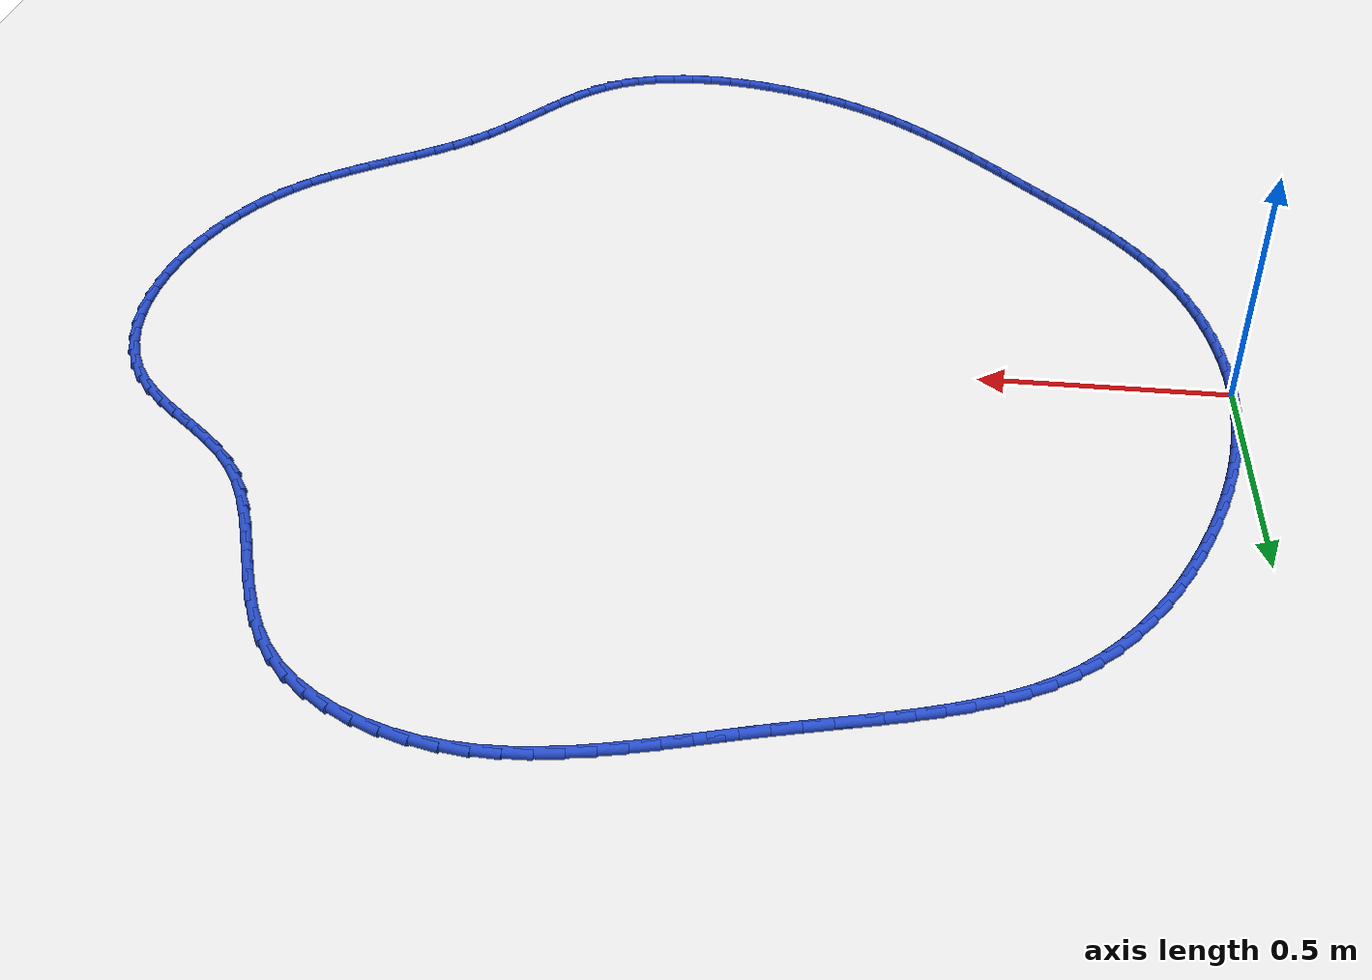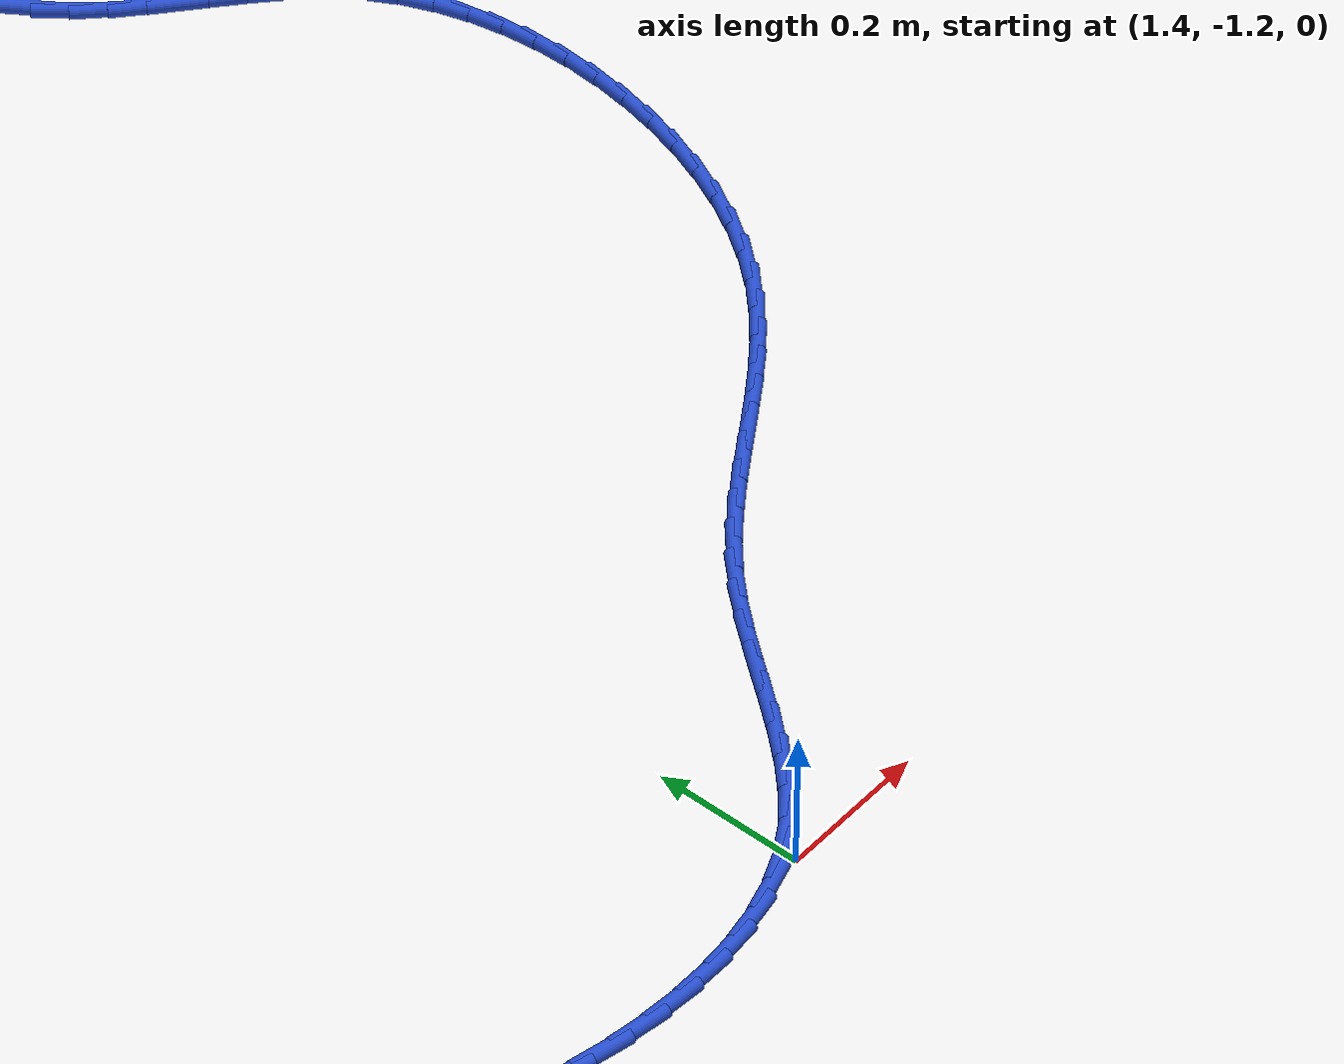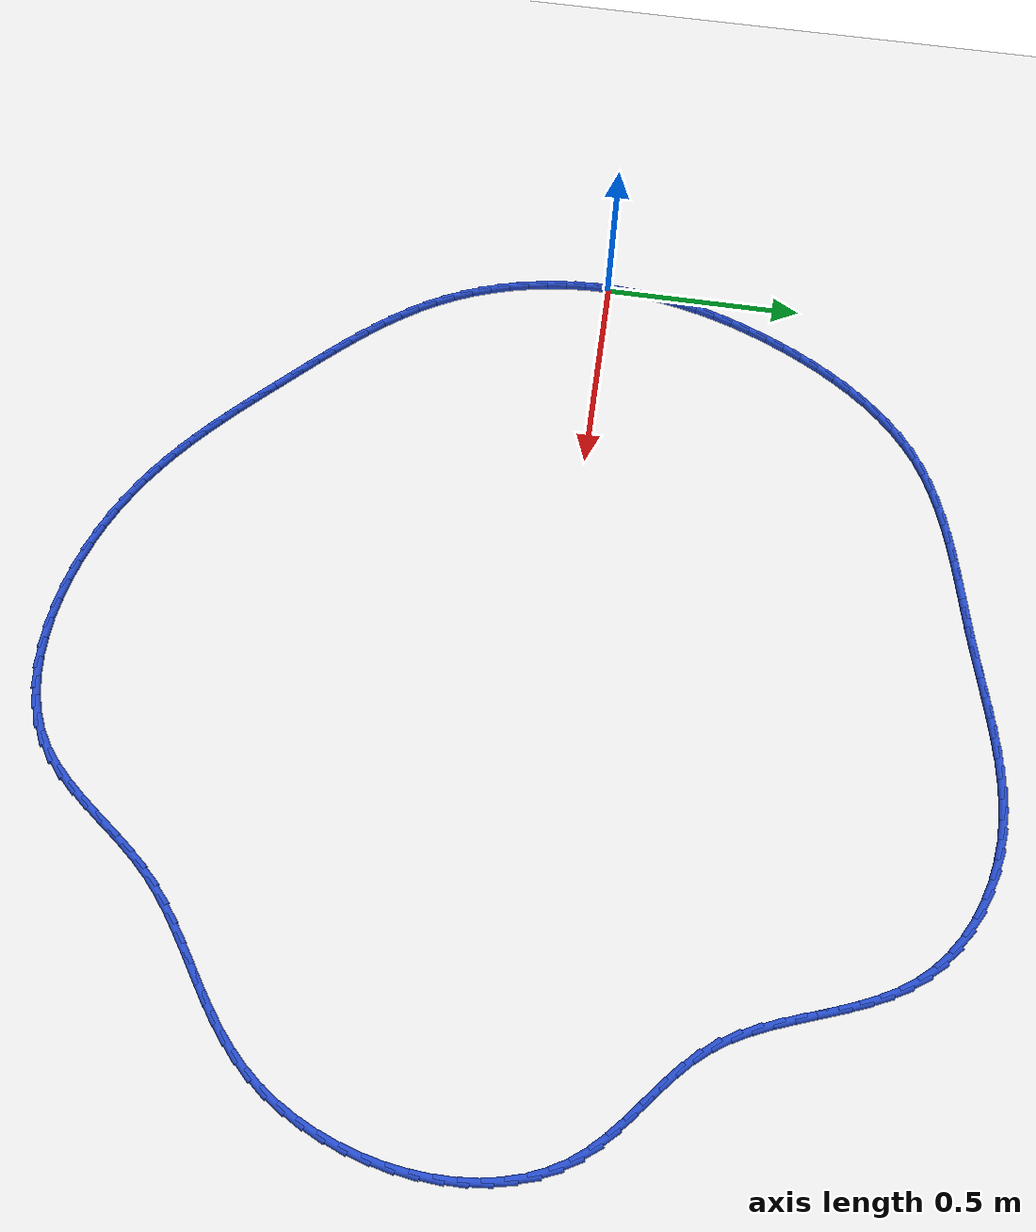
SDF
<sdf version="1.6">
 <world name="default">
  <light name="sun" type="directional">
   <pose>0 0 10 0 -0 0</pose>
   <diffuse>0.8 0.8 0.8 1</diffuse>
   <specular>0.2 0.2 0.2 1</specular>
   <attenuation>
    <range>1000</range>
    <constant>0.9</constant>
    <linear>0.01</linear>
    <quadratic>0.001</quadratic>
   </attenuation>
   <direction>-0.5 0.1 -0.9</direction>
  </light>
  <model name="ground_plane">
   <static>1</static>
   <link name="link">
    <collision name="collision">
     <geometry><plane><normal>0 0 1</normal><size>100 100</size></plane></geometry>
     <surface><friction><ode><mu>100</mu><mu2>50</mu2></ode></friction></surface>
    </collision>
    <visual name="visual">
     <cast_shadows>0</cast_shadows>
     <geometry><plane><normal>0 0 1</normal><size>100 100</size></plane></geometry>
     <material>
      <script><uri>file://media/materials/scripts/gazebo.material</uri><name>Gazebo/WhiteGlow</name></script>
     </material>
    </visual>
   </link>
  </model>
  <gravity>0 0 -9.8</gravity>
  <magnetic_field>6e-06 2.3e-05 -4.2e-05</magnetic_field>
  <atmosphere type="adiabatic"/>
  <physics name="default_physics" default="0" type="ode">
   <max_step_size>0.001</max_step_size>
   <real_time_factor>1</real_time_factor>
   <real_time_update_rate>1000</real_time_update_rate>
  </physics>
  <scene><ambient>0.4 0.4 0.4 1</ambient><background>0.7 0.7 0.7 1</background><shadows>1</shadows></scene>
  <spherical_coordinates>
   <surface_model>EARTH_WGS84</surface_model>
   <latitude_deg>0</latitude_deg>
   <longitude_deg>0</longitude_deg>
   <elevation>0</elevation>
   <heading_deg>0</heading_deg>
  </spherical_coordinates>
  <model name="line">
   <link name="link_0">
    <pose>-3.8163916471489756e-17 0.0 0.01 0 1.57 1.53081087506077</pose>
    <collision name="collision">
     <geometry><cylinder><radius>0.01</radius><length>0.08</length></cylinder></geometry>
    </collision>
    <visual name="visual">
     <material>
      <script><name>Gazebo/Blue</name><uri>file://media/materials/scripts/gazebo.material</uri></script>
     </material>
     <geometry><cylinder><radius>0.01</radius><length>0.08</length></cylinder></geometry>
    </visual>
   </link>
   <link name="link_1">
    <pose>0.001979722527505519 0.04948468118032241 0.01 0 1.57 1.4807791218871105</pose>
    <collision name="collision">
     <geometry><cylinder><radius>0.01</radius><length>0.08</length></cylinder></geometry>
    </collision>
    <visual name="visual">
     <material>
      <script><name>Gazebo/Blue</name><uri>file://media/materials/scripts/gazebo.material</uri></script>
     </material>
     <geometry><cylinder><radius>0.01</radius><length>0.08</length></cylinder></geometry>
    </visual>
   </link>
   <link name="link_2">
    <pose>0.0064161780831841105 0.09863601921336904 0.01 0 1.57 1.4322933718045248</pose>
    <collision name="collision">
     <geometry><cylinder><radius>0.01</radius><length>0.08</length></cylinder></geometry>
    </collision>
    <visual name="visual">
     <material>
      <script><name>Gazebo/Blue</name><uri>file://media/materials/scripts/gazebo.material</uri></script>
     </material>
     <geometry><cylinder><radius>0.01</radius><length>0.08</length></cylinder></geometry>
    </visual>
   </link>
   <link name="link_3">
    <pose>0.013221445217248372 0.14745588793199746 0.01 0 1.57 1.3855633104081833</pose>
    <collision name="collision">
     <geometry><cylinder><radius>0.01</radius><length>0.08</length></cylinder></geometry>
    </collision>
    <visual name="visual">
     <material>
      <script><name>Gazebo/Blue</name><uri>file://media/materials/scripts/gazebo.material</uri></script>
     </material>
     <geometry><cylinder><radius>0.01</radius><length>0.08</length></cylinder></geometry>
    </visual>
   </link>
   <link name="link_4">
    <pose>0.022307602479910926 0.1959461611690652 0.01 0 1.57 1.3407533342091134</pose>
    <collision name="collision">
     <geometry><cylinder><radius>0.01</radius><length>0.08</length></cylinder></geometry>
    </collision>
    <visual name="visual">
     <material>
      <script><name>Gazebo/Blue</name><uri>file://media/materials/scripts/gazebo.material</uri></script>
     </material>
     <geometry><cylinder><radius>0.01</radius><length>0.08</length></cylinder></geometry>
    </visual>
   </link>
   <link name="link_5">
    <pose>0.033586728421384465 0.24410871275742999 0.01 0 1.57 1.297983495147994</pose>
    <collision name="collision">
     <geometry><cylinder><radius>0.01</radius><length>0.08</length></cylinder></geometry>
    </collision>
    <visual name="visual">
     <material>
      <script><name>Gazebo/Blue</name><uri>file://media/materials/scripts/gazebo.material</uri></script>
     </material>
     <geometry><cylinder><radius>0.01</radius><length>0.08</length></cylinder></geometry>
    </visual>
   </link>
   <link name="link_6">
    <pose>0.04697090159188157 0.2919454165299492 0.01 0 1.57 1.2573325092678005</pose>
    <collision name="collision">
     <geometry><cylinder><radius>0.01</radius><length>0.08</length></cylinder></geometry>
    </collision>
    <visual name="visual">
     <material>
      <script><name>Gazebo/Blue</name><uri>file://media/materials/scripts/gazebo.material</uri></script>
     </material>
     <geometry><cylinder><radius>0.01</radius><length>0.08</length></cylinder></geometry>
    </visual>
   </link>
   <link name="link_7">
    <pose>0.06237220054161491 0.33945814631948057 0.01 0 1.57 1.2188421979531288</pose>
    <collision name="collision">
     <geometry><cylinder><radius>0.01</radius><length>0.08</length></cylinder></geometry>
    </collision>
    <visual name="visual">
     <material>
      <script><name>Gazebo/Blue</name><uri>file://media/materials/scripts/gazebo.material</uri></script>
     </material>
     <geometry><cylinder><radius>0.01</radius><length>0.08</length></cylinder></geometry>
    </visual>
   </link>
   <link name="link_8">
    <pose>0.07970270382079712 0.38664877595888164 0.01 0 1.57 1.1825227483022343</pose>
    <collision name="collision">
     <geometry><cylinder><radius>0.01</radius><length>0.08</length></cylinder></geometry>
    </collision>
    <visual name="visual">
     <material>
      <script><name>Gazebo/Blue</name><uri>file://media/materials/scripts/gazebo.material</uri></script>
     </material>
     <geometry><cylinder><radius>0.01</radius><length>0.08</length></cylinder></geometry>
    </visual>
   </link>
   <link name="link_9">
    <pose>0.09887448997964086 0.43351917928101014 0.01 0 1.57 1.147494360723241</pose>
    <collision name="collision">
     <geometry><cylinder><radius>0.01</radius><length>0.08</length></cylinder></geometry>
    </collision>
    <visual name="visual">
     <material>
      <script><name>Gazebo/Blue</name><uri>file://media/materials/scripts/gazebo.material</uri></script>
     </material>
     <geometry><cylinder><radius>0.01</radius><length>0.08</length></cylinder></geometry>
    </visual>
   </link>
   <link name="link_10">
    <pose>0.11982236632792301 0.48001433748194094 0.01 0 1.57 1.1100176047385018</pose>
    <collision name="collision">
     <geometry><cylinder><radius>0.01</radius><length>0.08</length></cylinder></geometry>
    </collision>
    <visual name="visual">
     <material>
      <script><name>Gazebo/Blue</name><uri>file://media/materials/scripts/gazebo.material</uri></script>
     </material>
     <geometry><cylinder><radius>0.01</radius><length>0.08</length></cylinder></geometry>
    </visual>
   </link>
   <link name="link_11">
    <pose>0.14257420913017707 0.525846269715818 0.01 0 1.57 1.0687088998159535</pose>
    <collision name="collision">
     <geometry><cylinder><radius>0.01</radius><length>0.08</length></cylinder></geometry>
    </collision>
    <visual name="visual">
     <material>
      <script><name>Gazebo/Blue</name><uri>file://media/materials/scripts/gazebo.material</uri></script>
     </material>
     <geometry><cylinder><radius>0.01</radius><length>0.08</length></cylinder></geometry>
    </visual>
   </link>
   <link name="link_12">
    <pose>0.16718171306497284 0.5706673749725314 0.01 0 1.57 1.0230122690982648</pose>
    <collision name="collision">
     <geometry><cylinder><radius>0.01</radius><length>0.08</length></cylinder></geometry>
    </collision>
    <visual name="visual">
     <material>
      <script><name>Gazebo/Blue</name><uri>file://media/materials/scripts/gazebo.material</uri></script>
     </material>
     <geometry><cylinder><radius>0.01</radius><length>0.08</length></cylinder></geometry>
    </visual>
   </link>
   <link name="link_13">
    <pose>0.19369657282194294 0.6141300522142797 0.01 0 1.57 0.972320734226884</pose>
    <collision name="collision">
     <geometry><cylinder><radius>0.01</radius><length>0.08</length></cylinder></geometry>
    </collision>
    <visual name="visual">
     <material>
      <script><name>Gazebo/Blue</name><uri>file://media/materials/scripts/gazebo.material</uri></script>
     </material>
     <geometry><cylinder><radius>0.01</radius><length>0.08</length></cylinder></geometry>
    </visual>
   </link>
   <link name="link_14">
    <pose>0.2221704830907201 0.6558867004032614 0.01 0 1.57 0.915989460977842</pose>
    <collision name="collision">
     <geometry><cylinder><radius>0.01</radius><length>0.08</length></cylinder></geometry>
    </collision>
    <visual name="visual">
     <material>
      <script><name>Gazebo/Blue</name><uri>file://media/materials/scripts/gazebo.material</uri></script>
     </material>
     <geometry><cylinder><radius>0.01</radius><length>0.08</length></cylinder></geometry>
    </visual>
   </link>
   <link name="link_15">
    <pose>0.25265513856093696 0.6955897185016748 0.01 0 1.57 0.8533644342717482</pose>
    <collision name="collision">
     <geometry><cylinder><radius>0.01</radius><length>0.08</length></cylinder></geometry>
    </collision>
    <visual name="visual">
     <material>
      <script><name>Gazebo/Blue</name><uri>file://media/materials/scripts/gazebo.material</uri></script>
     </material>
     <geometry><cylinder><radius>0.01</radius><length>0.08</length></cylinder></geometry>
    </visual>
   </link>
   <link name="link_16">
    <pose>0.2852022339222263 0.7328915054717189 0.01 0 1.57 0.7838338157106821</pose>
    <collision name="collision">
     <geometry><cylinder><radius>0.01</radius><length>0.08</length></cylinder></geometry>
    </collision>
    <visual name="visual">
     <material>
      <script><name>Gazebo/Blue</name><uri>file://media/materials/scripts/gazebo.material</uri></script>
     </material>
     <geometry><cylinder><radius>0.01</radius><length>0.08</length></cylinder></geometry>
    </visual>
   </link>
   <link name="link_17">
    <pose>0.31986346386422077 0.7674444602755917 0.01 0 1.57 0.7069092411978829</pose>
    <collision name="collision">
     <geometry><cylinder><radius>0.01</radius><length>0.08</length></cylinder></geometry>
    </collision>
    <visual name="visual">
     <material>
      <script><name>Gazebo/Blue</name><uri>file://media/materials/scripts/gazebo.material</uri></script>
     </material>
     <geometry><cylinder><radius>0.01</radius><length>0.08</length></cylinder></geometry>
    </visual>
   </link>
   <link name="link_18">
    <pose>0.35669052307655286 0.7989009818754916 0.01 0 1.57 0.6224150532274418</pose>
    <collision name="collision">
     <geometry><cylinder><radius>0.01</radius><length>0.08</length></cylinder></geometry>
    </collision>
    <visual name="visual">
     <material>
      <script><name>Gazebo/Blue</name><uri>file://media/materials/scripts/gazebo.material</uri></script>
     </material>
     <geometry><cylinder><radius>0.01</radius><length>0.08</length></cylinder></geometry>
    </visual>
   </link>
   <link name="link_19">
    <pose>0.39573379636541733 0.8269169212588227 0.01 0 1.57 0.5365468488485532</pose>
    <collision name="collision">
     <geometry><cylinder><radius>0.01</radius><length>0.08</length></cylinder></geometry>
    </collision>
    <visual name="visual">
     <material>
      <script><name>Gazebo/Blue</name><uri>file://media/materials/scripts/gazebo.material</uri></script>
     </material>
     <geometry><cylinder><radius>0.01</radius><length>0.08</length></cylinder></geometry>
    </visual>
   </link>
   <link name="link_20">
    <pose>0.43693913742727486 0.8514236073791587 0.01 0 1.57 0.4605530182431533</pose>
    <collision name="collision">
     <geometry><cylinder><radius>0.01</radius><length>0.08</length></cylinder></geometry>
    </collision>
    <visual name="visual">
     <material>
      <script><name>Gazebo/Blue</name><uri>file://media/materials/scripts/gazebo.material</uri></script>
     </material>
     <geometry><cylinder><radius>0.01</radius><length>0.08</length></cylinder></geometry>
    </visual>
   </link>
   <link name="link_21">
    <pose>0.4800733864922416 0.8728241355929346 0.01 0 1.57 0.39615801604458734</pose>
    <collision name="collision">
     <geometry><cylinder><radius>0.01</radius><length>0.08</length></cylinder></geometry>
    </collision>
    <visual name="visual">
     <material>
      <script><name>Gazebo/Blue</name><uri>file://media/materials/scripts/gazebo.material</uri></script>
     </material>
     <geometry><cylinder><radius>0.01</radius><length>0.08</length></cylinder></geometry>
    </visual>
   </link>
   <link name="link_22">
    <pose>0.5248858121714914 0.8915679089429837 0.01 0 1.57 0.3434493236026865</pose>
    <collision name="collision">
     <geometry><cylinder><radius>0.01</radius><length>0.08</length></cylinder></geometry>
    </collision>
    <visual name="visual">
     <material>
      <script><name>Gazebo/Blue</name><uri>file://media/materials/scripts/gazebo.material</uri></script>
     </material>
     <geometry><cylinder><radius>0.01</radius><length>0.08</length></cylinder></geometry>
    </visual>
   </link>
   <link name="link_23">
    <pose>0.5711256830761985 0.90810433047214 0.01 0 1.57 0.30213133555002225</pose>
    <collision name="collision">
     <geometry><cylinder><radius>0.01</radius><length>0.08</length></cylinder></geometry>
    </collision>
    <visual name="visual">
     <material>
      <script><name>Gazebo/Blue</name><uri>file://media/materials/scripts/gazebo.material</uri></script>
     </material>
     <geometry><cylinder><radius>0.01</radius><length>0.08</length></cylinder></geometry>
    </visual>
   </link>
   <link name="link_24">
    <pose>0.6185422678175366 0.9228828032232371 0.01 0 1.57 0.2717424104209548</pose>
    <collision name="collision">
     <geometry><cylinder><radius>0.01</radius><length>0.08</length></cylinder></geometry>
    </collision>
    <visual name="visual">
     <material>
      <script><name>Gazebo/Blue</name><uri>file://media/materials/scripts/gazebo.material</uri></script>
     </material>
     <geometry><cylinder><radius>0.01</radius><length>0.08</length></cylinder></geometry>
    </visual>
   </link>
   <link name="link_25">
    <pose>0.6668848350066798 0.9363527302391085 0.01 0 1.57 0.2518086556088177</pose>
    <collision name="collision">
     <geometry><cylinder><radius>0.01</radius><length>0.08</length></cylinder></geometry>
    </collision>
    <visual name="visual">
     <material>
      <script><name>Gazebo/Blue</name><uri>file://media/materials/scripts/gazebo.material</uri></script>
     </material>
     <geometry><cylinder><radius>0.01</radius><length>0.08</length></cylinder></geometry>
    </visual>
   </link>
   <link name="link_26">
    <pose>0.7159026532548021 0.9489635145625879 0.01 0 1.57 0.241939390597196</pose>
    <collision name="collision">
     <geometry><cylinder><radius>0.01</radius><length>0.08</length></cylinder></geometry>
    </collision>
    <visual name="visual">
     <material>
      <script><name>Gazebo/Blue</name><uri>file://media/materials/scripts/gazebo.material</uri></script>
     </material>
     <geometry><cylinder><radius>0.01</radius><length>0.08</length></cylinder></geometry>
    </visual>
   </link>
   <link name="link_27">
    <pose>0.7653449911730771 0.9611645592365086 0.01 0 1.57 0.241878161584756</pose>
    <collision name="collision">
     <geometry><cylinder><radius>0.01</radius><length>0.08</length></cylinder></geometry>
    </collision>
    <visual name="visual">
     <material>
      <script><name>Gazebo/Blue</name><uri>file://media/materials/scripts/gazebo.material</uri></script>
     </material>
     <geometry><cylinder><radius>0.01</radius><length>0.08</length></cylinder></geometry>
    </visual>
   </link>
   <link name="link_28">
    <pose>0.8149611173726793 0.9734052673037049 0.01 0 1.57 0.2515210322019817</pose>
    <collision name="collision">
     <geometry><cylinder><radius>0.01</radius><length>0.08</length></cylinder></geometry>
    </collision>
    <visual name="visual">
     <material>
      <script><name>Gazebo/Blue</name><uri>file://media/materials/scripts/gazebo.material</uri></script>
     </material>
     <geometry><cylinder><radius>0.01</radius><length>0.08</length></cylinder></geometry>
    </visual>
   </link>
   <link name="link_29">
    <pose>0.8645003147983724 0.9861349959404173 0.01 0 1.57 0.2668905871740424</pose>
    <collision name="collision">
     <geometry><cylinder><radius>0.01</radius><length>0.08</length></cylinder></geometry>
    </collision>
    <visual name="visual">
     <material>
      <script><name>Gazebo/Blue</name><uri>file://media/materials/scripts/gazebo.material</uri></script>
     </material>
     <geometry><cylinder><radius>0.01</radius><length>0.08</length></cylinder></geometry>
    </visual>
   </link>
   <link name="link_30">
    <pose>0.9137731926237459 0.9996068622212584 0.01 0 1.57 0.2748353361437529</pose>
    <collision name="collision">
     <geometry><cylinder><radius>0.01</radius><length>0.08</length></cylinder></geometry>
    </collision>
    <visual name="visual">
     <material>
      <script><name>Gazebo/Blue</name><uri>file://media/materials/scripts/gazebo.material</uri></script>
     </material>
     <geometry><cylinder><radius>0.01</radius><length>0.08</length></cylinder></geometry>
    </visual>
   </link>
   <link name="link_31">
    <pose>0.9627920031078606 1.0134287379425344 0.01 0 1.57 0.2725943795558558</pose>
    <collision name="collision">
     <geometry><cylinder><radius>0.01</radius><length>0.08</length></cylinder></geometry>
    </collision>
    <visual name="visual">
     <material>
      <script><name>Gazebo/Blue</name><uri>file://media/materials/scripts/gazebo.material</uri></script>
     </material>
     <geometry><cylinder><radius>0.01</radius><length>0.08</length></cylinder></geometry>
    </visual>
   </link>
   <link name="link_32">
    <pose>1.0116103808861336 1.0270760738810756 0.01 0 1.57 0.26001071186416236</pose>
    <collision name="collision">
     <geometry><cylinder><radius>0.01</radius><length>0.08</length></cylinder></geometry>
    </collision>
    <visual name="visual">
     <material>
      <script><name>Gazebo/Blue</name><uri>file://media/materials/scripts/gazebo.material</uri></script>
     </material>
     <geometry><cylinder><radius>0.01</radius><length>0.08</length></cylinder></geometry>
    </visual>
   </link>
   <link name="link_33">
    <pose>1.0602819605939822 1.0400243208137119 0.01 0 1.57 0.2368251089408114</pose>
    <collision name="collision">
     <geometry><cylinder><radius>0.01</radius><length>0.08</length></cylinder></geometry>
    </collision>
    <visual name="visual">
     <material>
      <script><name>Gazebo/Blue</name><uri>file://media/materials/scripts/gazebo.material</uri></script>
     </material>
     <geometry><cylinder><radius>0.01</radius><length>0.08</length></cylinder></geometry>
    </visual>
   </link>
   <link name="link_34">
    <pose>1.1088603768668228 1.0517489295172742 0.01 0 1.57 0.20271159090095395</pose>
    <collision name="collision">
     <geometry><cylinder><radius>0.01</radius><length>0.08</length></cylinder></geometry>
    </collision>
    <visual name="visual">
     <material>
      <script><name>Gazebo/Blue</name><uri>file://media/materials/scripts/gazebo.material</uri></script>
     </material>
     <geometry><cylinder><radius>0.01</radius><length>0.08</length></cylinder></geometry>
    </visual>
   </link>
   <link name="link_35">
    <pose>1.1573992643400726 1.0617253507685922 0.01 0 1.57 0.1573537947079281</pose>
    <collision name="collision">
     <geometry><cylinder><radius>0.01</radius><length>0.08</length></cylinder></geometry>
    </collision>
    <visual name="visual">
     <material>
      <script><name>Gazebo/Blue</name><uri>file://media/materials/scripts/gazebo.material</uri></script>
     </material>
     <geometry><cylinder><radius>0.01</radius><length>0.08</length></cylinder></geometry>
    </visual>
   </link>
   <link name="link_36">
    <pose>1.2059522576491486 1.0694290353444964 0.01 0 1.57 0.10057119876426046</pose>
    <collision name="collision">
     <geometry><cylinder><radius>0.01</radius><length>0.08</length></cylinder></geometry>
    </collision>
    <visual name="visual">
     <material>
      <script><name>Gazebo/Blue</name><uri>file://media/materials/scripts/gazebo.material</uri></script>
     </material>
     <geometry><cylinder><radius>0.01</radius><length>0.08</length></cylinder></geometry>
    </visual>
   </link>
   <link name="link_37">
    <pose>1.2545729914294677 1.0743354340218167 0.01 0 1.57 0.03249768492827597</pose>
    <collision name="collision">
     <geometry><cylinder><radius>0.01</radius><length>0.08</length></cylinder></geometry>
    </collision>
    <visual name="visual">
     <material>
      <script><name>Gazebo/Blue</name><uri>file://media/materials/scripts/gazebo.material</uri></script>
     </material>
     <geometry><cylinder><radius>0.01</radius><length>0.08</length></cylinder></geometry>
    </visual>
   </link>
   <link name="link_38">
    <pose>1.3033151003164465 1.0759199975773834 0.01 0 1.57 -0.04620490824820704</pose>
    <collision name="collision">
     <geometry><cylinder><radius>0.01</radius><length>0.08</length></cylinder></geometry>
    </collision>
    <visual name="visual">
     <material>
      <script><name>Gazebo/Blue</name><uri>file://media/materials/scripts/gazebo.material</uri></script>
     </material>
     <geometry><cylinder><radius>0.01</radius><length>0.08</length></cylinder></geometry>
    </visual>
   </link>
   <link name="link_39">
    <pose>1.352232218945503 1.0736581767880269 0.01 0 1.57 -0.13413293280615798</pose>
    <collision name="collision">
     <geometry><cylinder><radius>0.01</radius><length>0.08</length></cylinder></geometry>
    </collision>
    <visual name="visual">
     <material>
      <script><name>Gazebo/Blue</name><uri>file://media/materials/scripts/gazebo.material</uri></script>
     </material>
     <geometry><cylinder><radius>0.01</radius><length>0.08</length></cylinder></geometry>
    </visual>
   </link>
   <link name="link_40">
    <pose>1.401376419201328 1.0670265017133975 0.01 0 1.57 -0.22668272803391348</pose>
    <collision name="collision">
     <geometry><cylinder><radius>0.01</radius><length>0.08</length></cylinder></geometry>
    </collision>
    <visual name="visual">
     <material>
      <script><name>Gazebo/Blue</name><uri>file://media/materials/scripts/gazebo.material</uri></script>
     </material>
     <geometry><cylinder><radius>0.01</radius><length>0.08</length></cylinder></geometry>
    </visual>
   </link>
   <link name="link_41">
    <pose>1.4505266011161937 1.0556901631399138 0.01 0 1.57 -0.3190634901556683</pose>
    <collision name="collision">
     <geometry><cylinder><radius>0.01</radius><length>0.08</length></cylinder></geometry>
    </collision>
    <visual name="visual">
     <material>
      <script><name>Gazebo/Blue</name><uri>file://media/materials/scripts/gazebo.material</uri></script>
     </material>
     <geometry><cylinder><radius>0.01</radius><length>0.08</length></cylinder></geometry>
    </visual>
   </link>
   <link name="link_42">
    <pose>1.4988785211215883 1.0397170884264384 0.01 0 1.57 -0.41366919996070306</pose>
    <collision name="collision">
     <geometry><cylinder><radius>0.01</radius><length>0.08</length></cylinder></geometry>
    </collision>
    <visual name="visual">
     <material>
      <script><name>Gazebo/Blue</name><uri>file://media/materials/scripts/gazebo.material</uri></script>
     </material>
     <geometry><cylinder><radius>0.01</radius><length>0.08</length></cylinder></geometry>
    </visual>
   </link>
   <link name="link_43">
    <pose>1.5455529595109843 1.0192269857158454 0.01 0 1.57 -0.5136144983648645</pose>
    <collision name="collision">
     <geometry><cylinder><radius>0.01</radius><length>0.08</length></cylinder></geometry>
    </collision>
    <visual name="visual">
     <material>
      <script><name>Gazebo/Blue</name><uri>file://media/materials/scripts/gazebo.material</uri></script>
     </material>
     <geometry><cylinder><radius>0.01</radius><length>0.08</length></cylinder></geometry>
    </visual>
   </link>
   <link name="link_44">
    <pose>1.5896706965778555 0.9943395631510091 0.01 0 1.57 -0.6219823300720324</pose>
    <collision name="collision">
     <geometry><cylinder><radius>0.01</radius><length>0.08</length></cylinder></geometry>
    </collision>
    <visual name="visual">
     <material>
      <script><name>Gazebo/Blue</name><uri>file://media/materials/scripts/gazebo.material</uri></script>
     </material>
     <geometry><cylinder><radius>0.01</radius><length>0.08</length></cylinder></geometry>
    </visual>
   </link>
   <link name="link_45">
    <pose>1.630352512615673 0.9651745288748044 0.01 0 1.57 -0.7417502772724007</pose>
    <collision name="collision">
     <geometry><cylinder><radius>0.01</radius><length>0.08</length></cylinder></geometry>
    </collision>
    <visual name="visual">
     <material>
      <script><name>Gazebo/Blue</name><uri>file://media/materials/scripts/gazebo.material</uri></script>
     </material>
     <geometry><cylinder><radius>0.01</radius><length>0.08</length></cylinder></geometry>
    </visual>
   </link>
   <link name="link_46">
    <pose>1.6667191879179102 0.9318515910301057 0.01 0 1.57 -0.8731737706783052</pose>
    <collision name="collision">
     <geometry><cylinder><radius>0.01</radius><length>0.08</length></cylinder></geometry>
    </collision>
    <visual name="visual">
     <material>
      <script><name>Gazebo/Blue</name><uri>file://media/materials/scripts/gazebo.material</uri></script>
     </material>
     <geometry><cylinder><radius>0.01</radius><length>0.08</length></cylinder></geometry>
    </visual>
   </link>
   <link name="link_47">
    <pose>1.6980058838474383 0.8945269816575713 0.01 0 1.57 -0.994179210123533</pose>
    <collision name="collision">
     <geometry><cylinder><radius>0.01</radius><length>0.08</length></cylinder></geometry>
    </collision>
    <visual name="visual">
     <material>
      <script><name>Gazebo/Blue</name><uri>file://media/materials/scripts/gazebo.material</uri></script>
     </material>
     <geometry><cylinder><radius>0.01</radius><length>0.08</length></cylinder></geometry>
    </visual>
   </link>
   <link name="link_48">
    <pose>1.7245513964961652 0.85370934287975 0.01 0 1.57 -1.0897222913817504</pose>
    <collision name="collision">
     <geometry><cylinder><radius>0.01</radius><length>0.08</length></cylinder></geometry>
    </collision>
    <visual name="visual">
     <material>
      <script><name>Gazebo/Blue</name><uri>file://media/materials/scripts/gazebo.material</uri></script>
     </material>
     <geometry><cylinder><radius>0.01</radius><length>0.08</length></cylinder></geometry>
    </visual>
   </link>
   <link name="link_49">
    <pose>1.7473120998541447 0.8101045203612101 0.01 0 1.57 -1.1592627033562999</pose>
    <collision name="collision">
     <geometry><cylinder><radius>0.01</radius><length>0.08</length></cylinder></geometry>
    </collision>
    <visual name="visual">
     <material>
      <script><name>Gazebo/Blue</name><uri>file://media/materials/scripts/gazebo.material</uri></script>
     </material>
     <geometry><cylinder><radius>0.01</radius><length>0.08</length></cylinder></geometry>
    </visual>
   </link>
   <link name="link_50">
    <pose>1.7672511432443432 0.764420523250109 0.01 0 1.57 -1.2039484873253772</pose>
    <collision name="collision">
     <geometry><cylinder><radius>0.01</radius><length>0.08</length></cylinder></geometry>
    </collision>
    <visual name="visual">
     <material>
      <script><name>Gazebo/Blue</name><uri>file://media/materials/scripts/gazebo.material</uri></script>
     </material>
     <geometry><cylinder><radius>0.01</radius><length>0.08</length></cylinder></geometry>
    </visual>
   </link>
   <link name="link_51">
    <pose>1.7853316759897284 0.7173653606946067 0.01 0 1.57 -1.2251187419603604</pose>
    <collision name="collision">
     <geometry><cylinder><radius>0.01</radius><length>0.08</length></cylinder></geometry>
    </collision>
    <visual name="visual">
     <material>
      <script><name>Gazebo/Blue</name><uri>file://media/materials/scripts/gazebo.material</uri></script>
     </material>
     <geometry><cylinder><radius>0.01</radius><length>0.08</length></cylinder></geometry>
    </visual>
   </link>
   <link name="link_52">
    <pose>1.802516847413267 0.6696470418428605 0.01 0 1.57 -1.2235610140664208</pose>
    <collision name="collision">
     <geometry><cylinder><radius>0.01</radius><length>0.08</length></cylinder></geometry>
    </collision>
    <visual name="visual">
     <material>
      <script><name>Gazebo/Blue</name><uri>file://media/materials/scripts/gazebo.material</uri></script>
     </material>
     <geometry><cylinder><radius>0.01</radius><length>0.08</length></cylinder></geometry>
    </visual>
   </link>
   <link name="link_53">
    <pose>1.8197698068379258 0.6219735758430299 0.01 0 1.57 -1.1992203350926671</pose>
    <collision name="collision">
     <geometry><cylinder><radius>0.01</radius><length>0.08</length></cylinder></geometry>
    </collision>
    <visual name="visual">
     <material>
      <script><name>Gazebo/Blue</name><uri>file://media/materials/scripts/gazebo.material</uri></script>
     </material>
     <geometry><cylinder><radius>0.01</radius><length>0.08</length></cylinder></geometry>
    </visual>
   </link>
   <link name="link_54">
    <pose>1.8380537035866713 0.5750529718432726 0.01 0 1.57 -1.1512197904056243</pose>
    <collision name="collision">
     <geometry><cylinder><radius>0.01</radius><length>0.08</length></cylinder></geometry>
    </collision>
    <visual name="visual">
     <material>
      <script><name>Gazebo/Blue</name><uri>file://media/materials/scripts/gazebo.material</uri></script>
     </material>
     <geometry><cylinder><radius>0.01</radius><length>0.08</length></cylinder></geometry>
    </visual>
   </link>
   <link name="link_55">
    <pose>1.8583316869824724 0.5295932389917475 0.01 0 1.57 -1.0782032874842342</pose>
    <collision name="collision">
     <geometry><cylinder><radius>0.01</radius><length>0.08</length></cylinder></geometry>
    </collision>
    <visual name="visual">
     <material>
      <script><name>Gazebo/Blue</name><uri>file://media/materials/scripts/gazebo.material</uri></script>
     </material>
     <geometry><cylinder><radius>0.01</radius><length>0.08</length></cylinder></geometry>
    </visual>
   </link>
   <link name="link_56">
    <pose>1.8815669063482938 0.4863023864366133 0.01 0 1.57 -0.979154454333042</pose>
    <collision name="collision">
     <geometry><cylinder><radius>0.01</radius><length>0.08</length></cylinder></geometry>
    </collision>
    <visual name="visual">
     <material>
      <script><name>Gazebo/Blue</name><uri>file://media/materials/scripts/gazebo.material</uri></script>
     </material>
     <geometry><cylinder><radius>0.01</radius><length>0.08</length></cylinder></geometry>
    </visual>
   </link>
   <link name="link_57">
    <pose>1.908722511007104 0.44588842332602785 0.01 0 1.57 -0.8627603080321099</pose>
    <collision name="collision">
     <geometry><cylinder><radius>0.01</radius><length>0.08</length></cylinder></geometry>
    </collision>
    <visual name="visual">
     <material>
      <script><name>Gazebo/Blue</name><uri>file://media/materials/scripts/gazebo.material</uri></script>
     </material>
     <geometry><cylinder><radius>0.01</radius><length>0.08</length></cylinder></geometry>
    </visual>
   </link>
   <link name="link_58">
    <pose>1.940449605453515 0.40882923274522465 0.01 0 1.57 -0.770514575392855</pose>
    <collision name="collision">
     <geometry><cylinder><radius>0.01</radius><length>0.08</length></cylinder></geometry>
    </collision>
    <visual name="visual">
     <material>
      <script><name>Gazebo/Blue</name><uri>file://media/materials/scripts/gazebo.material</uri></script>
     </material>
     <geometry><cylinder><radius>0.01</radius><length>0.08</length></cylinder></geometry>
    </visual>
   </link>
   <link name="link_59">
    <pose>1.975854157489885 0.37446319412046747 0.01 0 1.57 -0.7141520142694131</pose>
    <collision name="collision">
     <geometry><cylinder><radius>0.01</radius><length>0.08</length></cylinder></geometry>
    </collision>
    <visual name="visual">
     <material>
      <script><name>Gazebo/Blue</name><uri>file://media/materials/scripts/gazebo.material</uri></script>
     </material>
     <geometry><cylinder><radius>0.01</radius><length>0.08</length></cylinder></geometry>
    </visual>
   </link>
   <link name="link_60">
    <pose>2.013564753231257 0.3417766285894941 0.01 0 1.57 -0.6919314941801472</pose>
    <collision name="collision">
     <geometry><cylinder><radius>0.01</radius><length>0.08</length></cylinder></geometry>
    </collision>
    <visual name="visual">
     <material>
      <script><name>Gazebo/Blue</name><uri>file://media/materials/scripts/gazebo.material</uri></script>
     </material>
     <geometry><cylinder><radius>0.01</radius><length>0.08</length></cylinder></geometry>
    </visual>
   </link>
   <link name="link_61">
    <pose>2.0522098398991466 0.3097557548591764 0.01 0 1.57 -0.7028529340440991</pose>
    <collision name="collision">
     <geometry><cylinder><radius>0.01</radius><length>0.08</length></cylinder></geometry>
    </collision>
    <visual name="visual">
     <material>
      <script><name>Gazebo/Blue</name><uri>file://media/materials/scripts/gazebo.material</uri></script>
     </material>
     <geometry><cylinder><radius>0.01</radius><length>0.08</length></cylinder></geometry>
    </visual>
   </link>
   <link name="link_62">
    <pose>2.090417864715064 0.27738679163638674 0.01 0 1.57 -0.747364796307066</pose>
    <collision name="collision">
     <geometry><cylinder><radius>0.01</radius><length>0.08</length></cylinder></geometry>
    </collision>
    <visual name="visual">
     <material>
      <script><name>Gazebo/Blue</name><uri>file://media/materials/scripts/gazebo.material</uri></script>
     </material>
     <geometry><cylinder><radius>0.01</radius><length>0.08</length></cylinder></geometry>
    </visual>
   </link>
   <link name="link_63">
    <pose>2.126817274900524 0.2436559576279969 0.01 0 1.57 -0.8270216092875979</pose>
    <collision name="collision">
     <geometry><cylinder><radius>0.01</radius><length>0.08</length></cylinder></geometry>
    </collision>
    <visual name="visual">
     <material>
      <script><name>Gazebo/Blue</name><uri>file://media/materials/scripts/gazebo.material</uri></script>
     </material>
     <geometry><cylinder><radius>0.01</radius><length>0.08</length></cylinder></geometry>
    </visual>
   </link>
   <link name="link_64">
    <pose>2.160036517677037 0.2075494715408795 0.01 0 1.57 -0.9422131920682514</pose>
    <collision name="collision">
     <geometry><cylinder><radius>0.01</radius><length>0.08</length></cylinder></geometry>
    </collision>
    <visual name="visual">
     <material>
      <script><name>Gazebo/Blue</name><uri>file://media/materials/scripts/gazebo.material</uri></script>
     </material>
     <geometry><cylinder><radius>0.01</radius><length>0.08</length></cylinder></geometry>
    </visual>
   </link>
   <link name="link_65">
    <pose>2.1887293442940425 0.16807915091521944 0.01 0 1.57 -1.0714778468137658</pose>
    <collision name="collision">
     <geometry><cylinder><radius>0.01</radius><length>0.08</length></cylinder></geometry>
    </collision>
    <visual name="visual">
     <material>
      <script><name>Gazebo/Blue</name><uri>file://media/materials/scripts/gazebo.material</uri></script>
     </material>
     <geometry><cylinder><radius>0.01</radius><length>0.08</length></cylinder></geometry>
    </visual>
   </link>
   <link name="link_66">
    <pose>2.2122463387295386 0.12496176449180786 0.01 0 1.57 -1.1912126226966444</pose>
    <collision name="collision">
     <geometry><cylinder><radius>0.01</radius><length>0.08</length></cylinder></geometry>
    </collision>
    <visual name="visual">
     <material>
      <script><name>Gazebo/Blue</name><uri>file://media/materials/scripts/gazebo.material</uri></script>
     </material>
     <geometry><cylinder><radius>0.01</radius><length>0.08</length></cylinder></geometry>
    </visual>
   </link>
   <link name="link_67">
    <pose>2.2307054029706626 0.0786903386836411 0.01 0 1.57 -1.300282113759891</pose>
    <collision name="collision">
     <geometry><cylinder><radius>0.01</radius><length>0.08</length></cylinder></geometry>
    </collision>
    <visual name="visual">
     <material>
      <script><name>Gazebo/Blue</name><uri>file://media/materials/scripts/gazebo.material</uri></script>
     </material>
     <geometry><cylinder><radius>0.01</radius><length>0.08</length></cylinder></geometry>
    </visual>
   </link>
   <link name="link_68">
    <pose>2.2442638811306614 0.029797801551579513 0.01 0 1.57 -1.399576229106103</pose>
    <collision name="collision">
     <geometry><cylinder><radius>0.01</radius><length>0.08</length></cylinder></geometry>
    </collision>
    <visual name="visual">
     <material>
      <script><name>Gazebo/Blue</name><uri>file://media/materials/scripts/gazebo.material</uri></script>
     </material>
     <geometry><cylinder><radius>0.01</radius><length>0.08</length></cylinder></geometry>
    </visual>
   </link>
   <link name="link_69">
    <pose>2.253079117322785 -0.021182918843514767 0.01 0 1.57 -1.490465903702625</pose>
    <collision name="collision">
     <geometry><cylinder><radius>0.01</radius><length>0.08</length></cylinder></geometry>
    </collision>
    <visual name="visual">
     <material>
      <script><name>Gazebo/Blue</name><uri>file://media/materials/scripts/gazebo.material</uri></script>
     </material>
     <geometry><cylinder><radius>0.01</radius><length>0.08</length></cylinder></geometry>
    </visual>
   </link>
   <link name="link_70">
    <pose>2.2573084556602803 -0.07371889444078131 0.01 0 1.57 1.5670767450500969</pose>
    <collision name="collision">
     <geometry><cylinder><radius>0.01</radius><length>0.08</length></cylinder></geometry>
    </collision>
    <visual name="visual">
     <material>
      <script><name>Gazebo/Blue</name><uri>file://media/materials/scripts/gazebo.material</uri></script>
     </material>
     <geometry><cylinder><radius>0.01</radius><length>0.08</length></cylinder></geometry>
    </visual>
   </link>
   <link name="link_71">
    <pose>2.2571092402563964 -0.1272771971793581 0.01 0 1.57 1.4882715956242358</pose>
    <collision name="collision">
     <geometry><cylinder><radius>0.01</radius><length>0.08</length></cylinder></geometry>
    </collision>
    <visual name="visual">
     <material>
      <script><name>Gazebo/Blue</name><uri>file://media/materials/scripts/gazebo.material</uri></script>
     </material>
     <geometry><cylinder><radius>0.01</radius><length>0.08</length></cylinder></geometry>
    </visual>
   </link>
   <link name="link_72">
    <pose>2.2526388152243806 -0.1813248989983842 0.01 0 1.57 1.413159112111547</pose>
    <collision name="collision">
     <geometry><cylinder><radius>0.01</radius><length>0.08</length></cylinder></geometry>
    </collision>
    <visual name="visual">
     <material>
      <script><name>Gazebo/Blue</name><uri>file://media/materials/scripts/gazebo.material</uri></script>
     </material>
     <geometry><cylinder><radius>0.01</radius><length>0.08</length></cylinder></geometry>
    </visual>
   </link>
   <link name="link_73">
    <pose>2.244054524677481 -0.23532907183699922 0.01 0 1.57 1.3402451435796385</pose>
    <collision name="collision">
     <geometry><cylinder><radius>0.01</radius><length>0.08</length></cylinder></geometry>
    </collision>
    <visual name="visual">
     <material>
      <script><name>Gazebo/Blue</name><uri>file://media/materials/scripts/gazebo.material</uri></script>
     </material>
     <geometry><cylinder><radius>0.01</radius><length>0.08</length></cylinder></geometry>
    </visual>
   </link>
   <link name="link_74">
    <pose>2.231513712728946 -0.28875678763434026 0.01 0 1.57 1.2680767030884115</pose>
    <collision name="collision">
     <geometry><cylinder><radius>0.01</radius><length>0.08</length></cylinder></geometry>
    </collision>
    <visual name="visual">
     <material>
      <script><name>Gazebo/Blue</name><uri>file://media/materials/scripts/gazebo.material</uri></script>
     </material>
     <geometry><cylinder><radius>0.01</radius><length>0.08</length></cylinder></geometry>
    </visual>
   </link>
   <link name="link_75">
    <pose>2.2151737234920246 -0.341075118329547 0.01 0 1.57 1.1952087913250653</pose>
    <collision name="collision">
     <geometry><cylinder><radius>0.01</radius><length>0.08</length></cylinder></geometry>
    </collision>
    <visual name="visual">
     <material>
      <script><name>Gazebo/Blue</name><uri>file://media/materials/scripts/gazebo.material</uri></script>
     </material>
     <geometry><cylinder><radius>0.01</radius><length>0.08</length></cylinder></geometry>
    </visual>
   </link>
   <link name="link_76">
    <pose>2.195191901079964 -0.3917511358617581 0.01 0 1.57 1.1201651749893309</pose>
    <collision name="collision">
     <geometry><cylinder><radius>0.01</radius><length>0.08</length></cylinder></geometry>
    </collision>
    <visual name="visual">
     <material>
      <script><name>Gazebo/Blue</name><uri>file://media/materials/scripts/gazebo.material</uri></script>
     </material>
     <geometry><cylinder><radius>0.01</radius><length>0.08</length></cylinder></geometry>
    </visual>
   </link>
   <link name="link_77">
    <pose>2.171725589606012 -0.44025191217011217 0.01 0 1.57 1.041401470117852</pose>
    <collision name="collision">
     <geometry><cylinder><radius>0.01</radius><length>0.08</length></cylinder></geometry>
    </collision>
    <visual name="visual">
     <material>
      <script><name>Gazebo/Blue</name><uri>file://media/materials/scripts/gazebo.material</uri></script>
     </material>
     <geometry><cylinder><radius>0.01</radius><length>0.08</length></cylinder></geometry>
    </visual>
   </link>
   <link name="link_78">
    <pose>2.1449321331834166 -0.48604451919374897 0.01 0 1.57 0.957280943739161</pose>
    <collision name="collision">
     <geometry><cylinder><radius>0.01</radius><length>0.08</length></cylinder></geometry>
    </collision>
    <visual name="visual">
     <material>
      <script><name>Gazebo/Blue</name><uri>file://media/materials/scripts/gazebo.material</uri></script>
     </material>
     <geometry><cylinder><radius>0.01</radius><length>0.08</length></cylinder></geometry>
    </visual>
   </link>
   <link name="link_79">
    <pose>2.1149688759254275 -0.5285960288718057 0.01 0 1.57 0.8664858030551501</pose>
    <collision name="collision">
     <geometry><cylinder><radius>0.01</radius><length>0.08</length></cylinder></geometry>
    </collision>
    <visual name="visual">
     <material>
      <script><name>Gazebo/Blue</name><uri>file://media/materials/scripts/gazebo.material</uri></script>
     </material>
     <geometry><cylinder><radius>0.01</radius><length>0.08</length></cylinder></geometry>
    </visual>
   </link>
   <link name="link_80">
    <pose>2.0820000516932327 -0.5673973103852394 0.01 0 1.57 0.7780754131058806</pose>
    <collision name="collision">
     <geometry><cylinder><radius>0.01</radius><length>0.08</length></cylinder></geometry>
    </collision>
    <visual name="visual">
     <material>
      <script><name>Gazebo/Blue</name><uri>file://media/materials/scripts/gazebo.material</uri></script>
     </material>
     <geometry><cylinder><radius>0.01</radius><length>0.08</length></cylinder></geometry>
    </visual>
   </link>
   <link name="link_81">
    <pose>2.046358288488346 -0.6025208675571405 0.01 0 1.57 0.7042316357529733</pose>
    <collision name="collision">
     <geometry><cylinder><radius>0.01</radius><length>0.08</length></cylinder></geometry>
    </collision>
    <visual name="visual">
     <material>
      <script><name>Gazebo/Blue</name><uri>file://media/materials/scripts/gazebo.material</uri></script>
     </material>
     <geometry><cylinder><radius>0.01</radius><length>0.08</length></cylinder></geometry>
    </visual>
   </link>
   <link name="link_82">
    <pose>2.00855031710709 -0.6346405565887573 0.01 0 1.57 0.6471058755725223</pose>
    <collision name="collision">
     <geometry><cylinder><radius>0.01</radius><length>0.08</length></cylinder></geometry>
    </collision>
    <visual name="visual">
     <material>
      <script><name>Gazebo/Blue</name><uri>file://media/materials/scripts/gazebo.material</uri></script>
     </material>
     <geometry><cylinder><radius>0.01</radius><length>0.08</length></cylinder></geometry>
    </visual>
   </link>
   <link name="link_83">
    <pose>1.9690909002224433 -0.6644579758444303 0.01 0 1.57 0.60740320628714</pose>
    <collision name="collision">
     <geometry><cylinder><radius>0.01</radius><length>0.08</length></cylinder></geometry>
    </collision>
    <visual name="visual">
     <material>
      <script><name>Gazebo/Blue</name><uri>file://media/materials/scripts/gazebo.material</uri></script>
     </material>
     <geometry><cylinder><radius>0.01</radius><length>0.08</length></cylinder></geometry>
    </visual>
   </link>
   <link name="link_84">
    <pose>1.9284948005073845 -0.6926747236885022 0.01 0 1.57 0.5852934455836823</pose>
    <collision name="collision">
     <geometry><cylinder><radius>0.01</radius><length>0.08</length></cylinder></geometry>
    </collision>
    <visual name="visual">
     <material>
      <script><name>Gazebo/Blue</name><uri>file://media/materials/scripts/gazebo.material</uri></script>
     </material>
     <geometry><cylinder><radius>0.01</radius><length>0.08</length></cylinder></geometry>
    </visual>
   </link>
   <link name="link_85">
    <pose>1.8872767806348936 -0.7199923984853148 0.01 0 1.57 0.5807656980729812</pose>
    <collision name="collision">
     <geometry><cylinder><radius>0.01</radius><length>0.08</length></cylinder></geometry>
    </collision>
    <visual name="visual">
     <material>
      <script><name>Gazebo/Blue</name><uri>file://media/materials/scripts/gazebo.material</uri></script>
     </material>
     <geometry><cylinder><radius>0.01</radius><length>0.08</length></cylinder></geometry>
    </visual>
   </link>
   <link name="link_86">
    <pose>1.8459516032779482 -0.74711259859921 0.01 0 1.57 0.5938329818406481</pose>
    <collision name="collision">
     <geometry><cylinder><radius>0.01</radius><length>0.08</length></cylinder></geometry>
    </collision>
    <visual name="visual">
     <material>
      <script><name>Gazebo/Blue</name><uri>file://media/materials/scripts/gazebo.material</uri></script>
     </material>
     <geometry><cylinder><radius>0.01</radius><length>0.08</length></cylinder></geometry>
    </visual>
   </link>
   <link name="link_87">
    <pose>1.8050340311095265 -0.7747369223945297 0.01 0 1.57 0.6245744467583751</pose>
    <collision name="collision">
     <geometry><cylinder><radius>0.01</radius><length>0.08</length></cylinder></geometry>
    </collision>
    <visual name="visual">
     <material>
      <script><name>Gazebo/Blue</name><uri>file://media/materials/scripts/gazebo.material</uri></script>
     </material>
     <geometry><cylinder><radius>0.01</radius><length>0.08</length></cylinder></geometry>
    </visual>
   </link>
   <link name="link_88">
    <pose>1.765038826802609 -0.8035669682356151 0.01 0 1.57 0.6730133702398493</pose>
    <collision name="collision">
     <geometry><cylinder><radius>0.01</radius><length>0.08</length></cylinder></geometry>
    </collision>
    <visual name="visual">
     <material>
      <script><name>Gazebo/Blue</name><uri>file://media/materials/scripts/gazebo.material</uri></script>
     </material>
     <geometry><cylinder><radius>0.01</radius><length>0.08</length></cylinder></geometry>
    </visual>
   </link>
   <link name="link_89">
    <pose>1.7264807530301733 -0.8343043344868087 0.01 0 1.57 0.7388302728225601</pose>
    <collision name="collision">
     <geometry><cylinder><radius>0.01</radius><length>0.08</length></cylinder></geometry>
    </collision>
    <visual name="visual">
     <material>
      <script><name>Gazebo/Blue</name><uri>file://media/materials/scripts/gazebo.material</uri></script>
     </material>
     <geometry><cylinder><radius>0.01</radius><length>0.08</length></cylinder></geometry>
    </visual>
   </link>
   <link name="link_90">
    <pose>1.6898745724651993 -0.867650619512452 0.01 0 1.57 0.8154487511754153</pose>
    <collision name="collision">
     <geometry><cylinder><radius>0.01</radius><length>0.08</length></cylinder></geometry>
    </collision>
    <visual name="visual">
     <material>
      <script><name>Gazebo/Blue</name><uri>file://media/materials/scripts/gazebo.material</uri></script>
     </material>
     <geometry><cylinder><radius>0.01</radius><length>0.08</length></cylinder></geometry>
    </visual>
   </link>
   <link name="link_91">
    <pose>1.655574744582883 -0.9040764345221076 0.01 0 1.57 0.8739197145126936</pose>
    <collision name="collision">
     <geometry><cylinder><radius>0.01</radius><length>0.08</length></cylinder></geometry>
    </collision>
    <visual name="visual">
     <material>
      <script><name>Gazebo/Blue</name><uri>file://media/materials/scripts/gazebo.material</uri></script>
     </material>
     <geometry><cylinder><radius>0.01</radius><length>0.08</length></cylinder></geometry>
    </visual>
   </link>
   <link name="link_92">
    <pose>1.6231109900513339 -0.9428639922833624 0.01 0 1.57 0.9064613731167324</pose>
    <collision name="collision">
     <geometry><cylinder><radius>0.01</radius><length>0.08</length></cylinder></geometry>
    </collision>
    <visual name="visual">
     <material>
      <script><name>Gazebo/Blue</name><uri>file://media/materials/scripts/gazebo.material</uri></script>
     </material>
     <geometry><cylinder><radius>0.01</radius><length>0.08</length></cylinder></geometry>
    </visual>
   </link>
   <link name="link_93">
    <pose>1.5917485420508328 -0.9829143951858887 0.01 0 1.57 0.9141320548324732</pose>
    <collision name="collision">
     <geometry><cylinder><radius>0.01</radius><length>0.08</length></cylinder></geometry>
    </collision>
    <visual name="visual">
     <material>
      <script><name>Gazebo/Blue</name><uri>file://media/materials/scripts/gazebo.material</uri></script>
     </material>
     <geometry><cylinder><radius>0.01</radius><length>0.08</length></cylinder></geometry>
    </visual>
   </link>
   <link name="link_94">
    <pose>1.560752512223063 -1.0231285704896291 0.01 0 1.57 0.8969657389285842</pose>
    <collision name="collision">
     <geometry><cylinder><radius>0.01</radius><length>0.08</length></cylinder></geometry>
    </collision>
    <visual name="visual">
     <material>
      <script><name>Gazebo/Blue</name><uri>file://media/materials/scripts/gazebo.material</uri></script>
     </material>
     <geometry><cylinder><radius>0.01</radius><length>0.08</length></cylinder></geometry>
    </visual>
   </link>
   <link name="link_95">
    <pose>1.5293880122097046 -1.062407445454527 0.01 0 1.57 0.8538105511425578</pose>
    <collision name="collision">
     <geometry><cylinder><radius>0.01</radius><length>0.08</length></cylinder></geometry>
    </collision>
    <visual name="visual">
     <material>
      <script><name>Gazebo/Blue</name><uri>file://media/materials/scripts/gazebo.material</uri></script>
     </material>
     <geometry><cylinder><radius>0.01</radius><length>0.08</length></cylinder></geometry>
    </visual>
   </link>
   <link name="link_96">
    <pose>1.4969201536524412 -1.0996519473405235 0.01 0 1.57 0.7825472871015674</pose>
    <collision name="collision">
     <geometry><cylinder><radius>0.01</radius><length>0.08</length></cylinder></geometry>
    </collision>
    <visual name="visual">
     <material>
      <script><name>Gazebo/Blue</name><uri>file://media/materials/scripts/gazebo.material</uri></script>
     </material>
     <geometry><cylinder><radius>0.01</radius><length>0.08</length></cylinder></geometry>
    </visual>
   </link>
   <link name="link_97">
    <pose>1.4626140481929537 -1.1337630034075623 0.01 0 1.57 0.6809128308107175</pose>
    <collision name="collision">
     <geometry><cylinder><radius>0.01</radius><length>0.08</length></cylinder></geometry>
    </collision>
    <visual name="visual">
     <material>
      <script><name>Gazebo/Blue</name><uri>file://media/materials/scripts/gazebo.material</uri></script>
     </material>
     <geometry><cylinder><radius>0.01</radius><length>0.08</length></cylinder></geometry>
    </visual>
   </link>
   <link name="link_98">
    <pose>1.4257348074729237 -1.1636415409155856 0.01 0 1.57 0.5498027103677591</pose>
    <collision name="collision">
     <geometry><cylinder><radius>0.01</radius><length>0.08</length></cylinder></geometry>
    </collision>
    <visual name="visual">
     <material>
      <script><name>Gazebo/Blue</name><uri>file://media/materials/scripts/gazebo.material</uri></script>
     </material>
     <geometry><cylinder><radius>0.01</radius><length>0.08</length></cylinder></geometry>
    </visual>
   </link>
   <link name="link_99">
    <pose>1.3855941386962536 -1.1882410993240962 0.01 0 1.57 0.41310760041337397</pose>
    <collision name="collision">
     <geometry><cylinder><radius>0.01</radius><length>0.08</length></cylinder></geometry>
    </collision>
    <visual name="visual">
     <material>
      <script><name>Gazebo/Blue</name><uri>file://media/materials/scripts/gazebo.material</uri></script>
     </material>
     <geometry><cylinder><radius>0.01</radius><length>0.08</length></cylinder></geometry>
    </visual>
   </link>
   <link name="link_100">
    <pose>1.3421749383269368 -1.2072730744551334 0.01 0 1.57 0.28909607476197546</pose>
    <collision name="collision">
     <geometry><cylinder><radius>0.01</radius><length>0.08</length></cylinder></geometry>
    </collision>
    <visual name="visual">
     <material>
      <script><name>Gazebo/Blue</name><uri>file://media/materials/scripts/gazebo.material</uri></script>
     </material>
     <geometry><cylinder><radius>0.01</radius><length>0.08</length></cylinder></geometry>
    </visual>
   </link>
   <link name="link_101">
    <pose>1.2959637937342712 -1.2210175919660184 0.01 0 1.57 0.1784967612604907</pose>
    <collision name="collision">
     <geometry><cylinder><radius>0.01</radius><length>0.08</length></cylinder></geometry>
    </collision>
    <visual name="visual">
     <material>
      <script><name>Gazebo/Blue</name><uri>file://media/materials/scripts/gazebo.material</uri></script>
     </material>
     <geometry><cylinder><radius>0.01</radius><length>0.08</length></cylinder></geometry>
    </visual>
   </link>
   <link name="link_102">
    <pose>1.2474595202668146 -1.2297685844273165 0.01 0 1.57 0.0803734774781849</pose>
    <collision name="collision">
     <geometry><cylinder><radius>0.01</radius><length>0.08</length></cylinder></geometry>
    </collision>
    <visual name="visual">
     <material>
      <script><name>Gazebo/Blue</name><uri>file://media/materials/scripts/gazebo.material</uri></script>
     </material>
     <geometry><cylinder><radius>0.01</radius><length>0.08</length></cylinder></geometry>
    </visual>
   </link>
   <link name="link_103">
    <pose>1.1971609332731254 -1.233819984409593 0.01 0 1.57 -0.0068661816147244726</pose>
    <collision name="collision">
     <geometry><cylinder><radius>0.01</radius><length>0.08</length></cylinder></geometry>
    </collision>
    <visual name="visual">
     <material>
      <script><name>Gazebo/Blue</name><uri>file://media/materials/scripts/gazebo.material</uri></script>
     </material>
     <geometry><cylinder><radius>0.01</radius><length>0.08</length></cylinder></geometry>
    </visual>
   </link>
   <link name="link_104">
    <pose>1.1455668481017613 -1.2334657244834135 0.01 0 1.57 -0.08503820394435636</pose>
    <collision name="collision">
     <geometry><cylinder><radius>0.01</radius><length>0.08</length></cylinder></geometry>
    </collision>
    <visual name="visual">
     <material>
      <script><name>Gazebo/Blue</name><uri>file://media/materials/scripts/gazebo.material</uri></script>
     </material>
     <geometry><cylinder><radius>0.01</radius><length>0.08</length></cylinder></geometry>
    </visual>
   </link>
   <link name="link_105">
    <pose>1.0931760801012829 -1.228999737219344 0.01 0 1.57 -0.15594486901023868</pose>
    <collision name="collision">
     <geometry><cylinder><radius>0.01</radius><length>0.08</length></cylinder></geometry>
    </collision>
    <visual name="visual">
     <material>
      <script><name>Gazebo/Blue</name><uri>file://media/materials/scripts/gazebo.material</uri></script>
     </material>
     <geometry><cylinder><radius>0.01</radius><length>0.08</length></cylinder></geometry>
    </visual>
   </link>
   <link name="link_106">
    <pose>1.040487444620248 -1.2207159551879494 0.01 0 1.57 -0.22127662373898463</pose>
    <collision name="collision">
     <geometry><cylinder><radius>0.01</radius><length>0.08</length></cylinder></geometry>
    </collision>
    <visual name="visual">
     <material>
      <script><name>Gazebo/Blue</name><uri>file://media/materials/scripts/gazebo.material</uri></script>
     </material>
     <geometry><cylinder><radius>0.01</radius><length>0.08</length></cylinder></geometry>
    </visual>
   </link>
   <link name="link_107">
    <pose>0.9879997570072141 -1.2089083109597953 0.01 0 1.57 -0.28259715803222135</pose>
    <collision name="collision">
     <geometry><cylinder><radius>0.01</radius><length>0.08</length></cylinder></geometry>
    </collision>
    <visual name="visual">
     <material>
      <script><name>Gazebo/Blue</name><uri>file://media/materials/scripts/gazebo.material</uri></script>
     </material>
     <geometry><cylinder><radius>0.01</radius><length>0.08</length></cylinder></geometry>
    </visual>
   </link>
   <link name="link_108">
    <pose>0.9362118326107407 -1.1938707371054476 0.01 0 1.57 -0.34137414167679103</pose>
    <collision name="collision">
     <geometry><cylinder><radius>0.01</radius><length>0.08</length></cylinder></geometry>
    </collision>
    <visual name="visual">
     <material>
      <script><name>Gazebo/Blue</name><uri>file://media/materials/scripts/gazebo.material</uri></script>
     </material>
     <geometry><cylinder><radius>0.01</radius><length>0.08</length></cylinder></geometry>
    </visual>
   </link>
   <link name="link_109">
    <pose>0.8856224867793855 -1.1758971661954716 0.01 0 1.57 -0.39903572055412667</pose>
    <collision name="collision">
     <geometry><cylinder><radius>0.01</radius><length>0.08</length></cylinder></geometry>
    </collision>
    <visual name="visual">
     <material>
      <script><name>Gazebo/Blue</name><uri>file://media/materials/scripts/gazebo.material</uri></script>
     </material>
     <geometry><cylinder><radius>0.01</radius><length>0.08</length></cylinder></geometry>
    </visual>
   </link>
   <link name="link_110">
    <pose>0.8367305348617082 -1.1552815308004327 0.01 0 1.57 -0.45689526833160005</pose>
    <collision name="collision">
     <geometry><cylinder><radius>0.01</radius><length>0.08</length></cylinder></geometry>
    </collision>
    <visual name="visual">
     <material>
      <script><name>Gazebo/Blue</name><uri>file://media/materials/scripts/gazebo.material</uri></script>
     </material>
     <geometry><cylinder><radius>0.01</radius><length>0.08</length></cylinder></geometry>
    </visual>
   </link>
   <link name="link_111">
    <pose>0.790009562821984 -1.1323140687374673 0.01 0 1.57 -0.5136685503952924</pose>
    <collision name="collision">
     <geometry><cylinder><radius>0.01</radius><length>0.08</length></cylinder></geometry>
    </collision>
    <visual name="visual">
     <material>
      <script><name>Gazebo/Blue</name><uri>file://media/materials/scripts/gazebo.material</uri></script>
     </material>
     <geometry><cylinder><radius>0.01</radius><length>0.08</length></cylinder></geometry>
    </visual>
   </link>
   <link name="link_112">
    <pose>0.7455458258618485 -1.1072282946136822 0.01 0 1.57 -0.5670344957185391</pose>
    <collision name="collision">
     <geometry><cylinder><radius>0.01</radius><length>0.08</length></cylinder></geometry>
    </collision>
    <visual name="visual">
     <material>
      <script><name>Gazebo/Blue</name><uri>file://media/materials/scripts/gazebo.material</uri></script>
     </material>
     <geometry><cylinder><radius>0.01</radius><length>0.08</length></cylinder></geometry>
    </visual>
   </link>
   <link name="link_113">
    <pose>0.703122305253009 -1.0802133096497897 0.01 0 1.57 -0.6161654145687563</pose>
    <collision name="collision">
     <geometry><cylinder><radius>0.01</radius><length>0.08</length></cylinder></geometry>
    </collision>
    <visual name="visual">
     <material>
      <script><name>Gazebo/Blue</name><uri>file://media/materials/scripts/gazebo.material</uri></script>
     </material>
     <geometry><cylinder><radius>0.01</radius><length>0.08</length></cylinder></geometry>
    </visual>
   </link>
   <link name="link_114">
    <pose>0.6625138802879413 -1.0514570285605132 0.01 0 1.57 -0.660435735516479</pose>
    <collision name="collision">
     <geometry><cylinder><radius>0.01</radius><length>0.08</length></cylinder></geometry>
    </collision>
    <visual name="visual">
     <material>
      <script><name>Gazebo/Blue</name><uri>file://media/materials/scripts/gazebo.material</uri></script>
     </material>
     <geometry><cylinder><radius>0.01</radius><length>0.08</length></cylinder></geometry>
    </visual>
   </link>
   <link name="link_115">
    <pose>0.6234954302591198 -1.0211473660605757 0.01 0 1.57 -0.699377350561897</pose>
    <collision name="collision">
     <geometry><cylinder><radius>0.01</radius><length>0.08</length></cylinder></geometry>
    </collision>
    <visual name="visual">
     <material>
      <script><name>Gazebo/Blue</name><uri>file://media/materials/scripts/gazebo.material</uri></script>
     </material>
     <geometry><cylinder><radius>0.01</radius><length>0.08</length></cylinder></geometry>
    </visual>
   </link>
   <link name="link_116">
    <pose>0.5858418344590187 -0.9894722368647004 0.01 0 1.57 -0.7326668771373367</pose>
    <collision name="collision">
     <geometry><cylinder><radius>0.01</radius><length>0.08</length></cylinder></geometry>
    </collision>
    <visual name="visual">
     <material>
      <script><name>Gazebo/Blue</name><uri>file://media/materials/scripts/gazebo.material</uri></script>
     </material>
     <geometry><cylinder><radius>0.01</radius><length>0.08</length></cylinder></geometry>
    </visual>
   </link>
   <link name="link_117">
    <pose>0.549327972180112 -0.9566195556876098 0.01 0 1.57 -0.7601027052376449</pose>
    <collision name="collision">
     <geometry><cylinder><radius>0.01</radius><length>0.08</length></cylinder></geometry>
    </collision>
    <visual name="visual">
     <material>
      <script><name>Gazebo/Blue</name><uri>file://media/materials/scripts/gazebo.material</uri></script>
     </material>
     <geometry><cylinder><radius>0.01</radius><length>0.08</length></cylinder></geometry>
    </visual>
   </link>
   <link name="link_118">
    <pose>0.5137287227148756 -0.9227772372440284 0.01 0 1.57 -0.7815778821567781</pose>
    <collision name="collision">
     <geometry><cylinder><radius>0.01</radius><length>0.08</length></cylinder></geometry>
    </collision>
    <visual name="visual">
     <material>
      <script><name>Gazebo/Blue</name><uri>file://media/materials/scripts/gazebo.material</uri></script>
     </material>
     <geometry><cylinder><radius>0.01</radius><length>0.08</length></cylinder></geometry>
    </visual>
   </link>
   <link name="link_119">
    <pose>0.4788189653557832 -0.8881331962486783 0.01 0 1.57 -0.7970536637883447</pose>
    <collision name="collision">
     <geometry><cylinder><radius>0.01</radius><length>0.08</length></cylinder></geometry>
    </collision>
    <visual name="visual">
     <material>
      <script><name>Gazebo/Blue</name><uri>file://media/materials/scripts/gazebo.material</uri></script>
     </material>
     <geometry><cylinder><radius>0.01</radius><length>0.08</length></cylinder></geometry>
    </visual>
   </link>
   <link name="link_120">
    <pose>0.4443735793953094 -0.8528753474162825 0.01 0 1.57 -0.8065369412714889</pose>
    <collision name="collision">
     <geometry><cylinder><radius>0.01</radius><length>0.08</length></cylinder></geometry>
    </collision>
    <visual name="visual">
     <material>
      <script><name>Gazebo/Blue</name><uri>file://media/materials/scripts/gazebo.material</uri></script>
     </material>
     <geometry><cylinder><radius>0.01</radius><length>0.08</length></cylinder></geometry>
    </visual>
   </link>
   <link name="link_121">
    <pose>0.41016744412592926 -0.8171916054615652 0.01 0 1.57 -0.8100633036550033</pose>
    <collision name="collision">
     <geometry><cylinder><radius>0.01</radius><length>0.08</length></cylinder></geometry>
    </collision>
    <visual name="visual">
     <material>
      <script><name>Gazebo/Blue</name><uri>file://media/materials/scripts/gazebo.material</uri></script>
     </material>
     <geometry><cylinder><radius>0.01</radius><length>0.08</length></cylinder></geometry>
    </visual>
   </link>
   <link name="link_122">
    <pose>0.3759754391884549 -0.7812698848670939 0.01 0 1.57 -0.8099681636429859</pose>
    <collision name="collision">
     <geometry><cylinder><radius>0.01</radius><length>0.08</length></cylinder></geometry>
    </collision>
    <visual name="visual">
     <material>
      <script><name>Gazebo/Blue</name><uri>file://media/materials/scripts/gazebo.material</uri></script>
     </material>
     <geometry><cylinder><radius>0.01</radius><length>0.08</length></cylinder></geometry>
    </visual>
   </link>
   <link name="link_123">
    <pose>0.34166838421716655 -0.7452341599042203 0.01 0 1.57 -0.814979259741752</pose>
    <collision name="collision">
     <geometry><cylinder><radius>0.01</radius><length>0.08</length></cylinder></geometry>
    </collision>
    <visual name="visual">
     <material>
      <script><name>Gazebo/Blue</name><uri>file://media/materials/scripts/gazebo.material</uri></script>
     </material>
     <geometry><cylinder><radius>0.01</radius><length>0.08</length></cylinder></geometry>
    </visual>
   </link>
   <link name="link_124">
    <pose>0.3074833070432797 -0.7089643415645641 0.01 0 1.57 -0.8271727270363326</pose>
    <collision name="collision">
     <geometry><cylinder><radius>0.01</radius><length>0.08</length></cylinder></geometry>
    </collision>
    <visual name="visual">
     <material>
      <script><name>Gazebo/Blue</name><uri>file://media/materials/scripts/gazebo.material</uri></script>
     </material>
     <geometry><cylinder><radius>0.01</radius><length>0.08</length></cylinder></geometry>
    </visual>
   </link>
   <link name="link_125">
    <pose>0.2737445985280172 -0.6722821168354541 0.01 0 1.57 -0.8466106097963475</pose>
    <collision name="collision">
     <geometry><cylinder><radius>0.01</radius><length>0.08</length></cylinder></geometry>
    </collision>
    <visual name="visual">
     <material>
      <script><name>Gazebo/Blue</name><uri>file://media/materials/scripts/gazebo.material</uri></script>
     </material>
     <geometry><cylinder><radius>0.01</radius><length>0.08</length></cylinder></geometry>
    </visual>
   </link>
   <link name="link_126">
    <pose>0.2407766495326015 -0.6350091727042174 0.01 0 1.57 -0.8734087612382713</pose>
    <collision name="collision">
     <geometry><cylinder><radius>0.01</radius><length>0.08</length></cylinder></geometry>
    </collision>
    <visual name="visual">
     <material>
      <script><name>Gazebo/Blue</name><uri>file://media/materials/scripts/gazebo.material</uri></script>
     </material>
     <geometry><cylinder><radius>0.01</radius><length>0.08</length></cylinder></geometry>
    </visual>
   </link>
   <link name="link_127">
    <pose>0.20890385091825683 -0.5969671961581833 0.01 0 1.57 -0.9077072288622362</pose>
    <collision name="collision">
     <geometry><cylinder><radius>0.01</radius><length>0.08</length></cylinder></geometry>
    </collision>
    <visual name="visual">
     <material>
      <script><name>Gazebo/Blue</name><uri>file://media/materials/scripts/gazebo.material</uri></script>
     </material>
     <geometry><cylinder><radius>0.01</radius><length>0.08</length></cylinder></geometry>
    </visual>
   </link>
   <link name="link_128">
    <pose>0.17845059354620565 -0.5579778741846791 0.01 0 1.57 -0.9496269083709507</pose>
    <collision name="collision">
     <geometry><cylinder><radius>0.01</radius><length>0.08</length></cylinder></geometry>
    </collision>
    <visual name="visual">
     <material>
      <script><name>Gazebo/Blue</name><uri>file://media/materials/scripts/gazebo.material</uri></script>
     </material>
     <geometry><cylinder><radius>0.01</radius><length>0.08</length></cylinder></geometry>
    </visual>
   </link>
   <link name="link_129">
    <pose>0.14974126827767092 -0.5178628937710328 0.01 0 1.57 -0.9992106076682364</pose>
    <collision name="collision">
     <geometry><cylinder><radius>0.01</radius><length>0.08</length></cylinder></geometry>
    </collision>
    <visual name="visual">
     <material>
      <script><name>Gazebo/Blue</name><uri>file://media/materials/scripts/gazebo.material</uri></script>
     </material>
     <geometry><cylinder><radius>0.01</radius><length>0.08</length></cylinder></geometry>
    </visual>
   </link>
   <link name="link_130">
    <pose>0.12310026597387583 -0.47644394190457273 0.01 0 1.57 -1.0563491892126509</pose>
    <collision name="collision">
     <geometry><cylinder><radius>0.01</radius><length>0.08</length></cylinder></geometry>
    </collision>
    <visual name="visual">
     <material>
      <script><name>Gazebo/Blue</name><uri>file://media/materials/scripts/gazebo.material</uri></script>
     </material>
     <geometry><cylinder><radius>0.01</radius><length>0.08</length></cylinder></geometry>
    </visual>
   </link>
   <link name="link_131">
    <pose>0.09885197746884411 -0.4335427056042994 0.01 0 1.57 -1.119032684332613</pose>
    <collision name="collision">
     <geometry><cylinder><radius>0.01</radius><length>0.08</length></cylinder></geometry>
    </collision>
    <visual name="visual">
     <material>
      <script><name>Gazebo/Blue</name><uri>file://media/materials/scripts/gazebo.material</uri></script>
     </material>
     <geometry><cylinder><radius>0.01</radius><length>0.08</length></cylinder></geometry>
    </visual>
   </link>
   <link name="link_132">
    <pose>0.0772622346529628 -0.38904906443972614 0.01 0 1.57 -1.1805253907014566</pose>
    <collision name="collision">
     <geometry><cylinder><radius>0.01</radius><length>0.08</length></cylinder></geometry>
    </collision>
    <visual name="visual">
     <material>
      <script><name>Gazebo/Blue</name><uri>file://media/materials/scripts/gazebo.material</uri></script>
     </material>
     <geometry><cylinder><radius>0.01</radius><length>0.08</length></cylinder></geometry>
    </visual>
   </link>
   <link name="link_133">
    <pose>0.058368054027493385 -0.343119356082426 0.01 0 1.57 -1.2394800943022848</pose>
    <collision name="collision">
     <geometry><cylinder><radius>0.01</radius><length>0.08</length></cylinder></geometry>
    </collision>
    <visual name="visual">
     <material>
      <script><name>Gazebo/Blue</name><uri>file://media/materials/scripts/gazebo.material</uri></script>
     </material>
     <geometry><cylinder><radius>0.01</radius><length>0.08</length></cylinder></geometry>
    </visual>
   </link>
   <link name="link_134">
    <pose>0.042150572128379464 -0.29597499105400626 0.01 0 1.57 -1.2962257383660838</pose>
    <collision name="collision">
     <geometry><cylinder><radius>0.01</radius><length>0.08</length></cylinder></geometry>
    </collision>
    <visual name="visual">
     <material>
      <script><name>Gazebo/Blue</name><uri>file://media/materials/scripts/gazebo.material</uri></script>
     </material>
     <geometry><cylinder><radius>0.01</radius><length>0.08</length></cylinder></geometry>
    </visual>
   </link>
   <link name="link_135">
    <pose>0.02859092549156437 -0.2478373798760738 0.01 0 1.57 -1.351116227000631</pose>
    <collision name="collision">
     <geometry><cylinder><radius>0.01</radius><length>0.08</length></cylinder></geometry>
    </collision>
    <visual name="visual">
     <material>
      <script><name>Gazebo/Blue</name><uri>file://media/materials/scripts/gazebo.material</uri></script>
     </material>
     <geometry><cylinder><radius>0.01</radius><length>0.08</length></cylinder></geometry>
    </visual>
   </link>
   <link name="link_136">
    <pose>0.017670250652992086 -0.19892793307023773 0.01 0 1.57 -1.4045215522306174</pose>
    <collision name="collision">
     <geometry><cylinder><radius>0.01</radius><length>0.08</length></cylinder></geometry>
    </collision>
    <visual name="visual">
     <material>
      <script><name>Gazebo/Blue</name><uri>file://media/materials/scripts/gazebo.material</uri></script>
     </material>
     <geometry><cylinder><radius>0.01</radius><length>0.08</length></cylinder></geometry>
    </visual>
   </link>
   <link name="link_137">
    <pose>0.00936968414860594 -0.14946806115810485 0.01 0 1.57 -1.4568226556102815</pose>
    <collision name="collision">
     <geometry><cylinder><radius>0.01</radius><length>0.08</length></cylinder></geometry>
    </collision>
    <visual name="visual">
     <material>
      <script><name>Gazebo/Blue</name><uri>file://media/materials/scripts/gazebo.material</uri></script>
     </material>
     <geometry><cylinder><radius>0.01</radius><length>0.08</length></cylinder></geometry>
    </visual>
   </link>
   <link name="link_138">
    <pose>0.0036703625143495013 -0.09967917466128268 0.01 0 1.57 -1.5084092674588687</pose>
    <collision name="collision">
     <geometry><cylinder><radius>0.01</radius><length>0.08</length></cylinder></geometry>
    </collision>
    <visual name="visual">
     <material>
      <script><name>Gazebo/Blue</name><uri>file://media/materials/scripts/gazebo.material</uri></script>
     </material>
     <geometry><cylinder><radius>0.01</radius><length>0.08</length></cylinder></geometry>
    </visual>
   </link>
   <link name="link_139">
    <pose>0.000553422286166309 -0.04978268410137875 0.01 0 1.57 -1.5596800219975133</pose>
    <collision name="collision">
     <geometry><cylinder><radius>0.01</radius><length>0.08</length></cylinder></geometry>
    </collision>
    <visual name="visual">
     <material>
      <script><name>Gazebo/Blue</name><uri>file://media/materials/scripts/gazebo.material</uri></script>
     </material>
     <geometry><cylinder><radius>0.01</radius><length>0.08</length></cylinder></geometry>
    </visual>
   </link>
   <link name="link_140">
    <pose>-4.5102810375396984e-17 1.1102230246251565e-16 0.01 0 1.57 1.5305484233798274</pose>
    <collision name="collision">
     <geometry><cylinder><radius>0.01</radius><length>0.08</length></cylinder></geometry>
    </collision>
    <visual name="visual">
     <material>
      <script><name>Gazebo/Blue</name><uri>file://media/materials/scripts/gazebo.material</uri></script>
     </material>
     <geometry><cylinder><radius>0.01</radius><length>0.08</length></cylinder></geometry>
    </visual>
   </link>
   <link name="link_141">
    <pose>0.0019912321917939894 0.04944746712124483 0.01 0 1.57 1.5305484233798277</pose>
    <collision name="collision">
     <geometry><cylinder><radius>0.01</radius><length>0.08</length></cylinder></geometry>
    </collision>
    <visual name="visual">
     <material>
      <script><name>Gazebo/Blue</name><uri>file://media/materials/scripts/gazebo.material</uri></script>
     </material>
     <geometry><cylinder><radius>0.01</radius><length>0.08</length></cylinder></geometry>
    </visual>
   </link>
  </model>
 </world>
</sdf>
